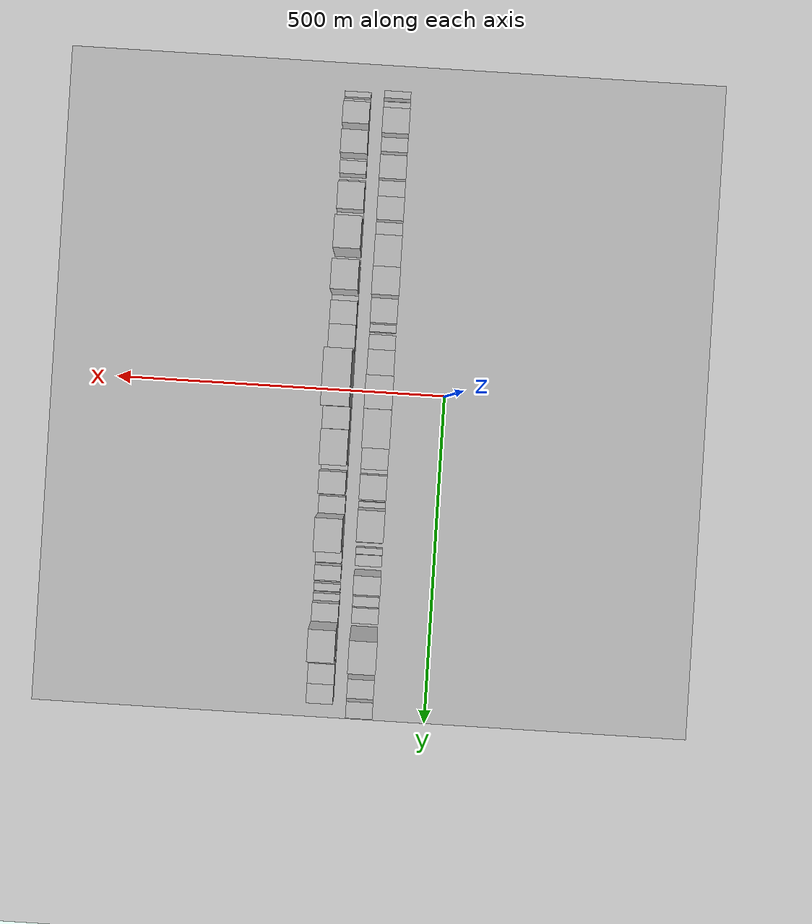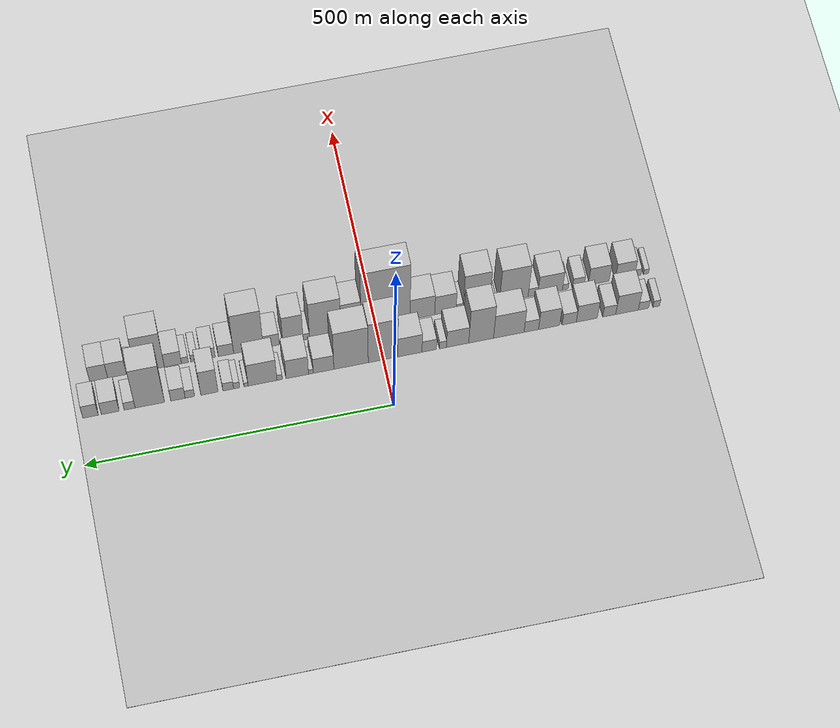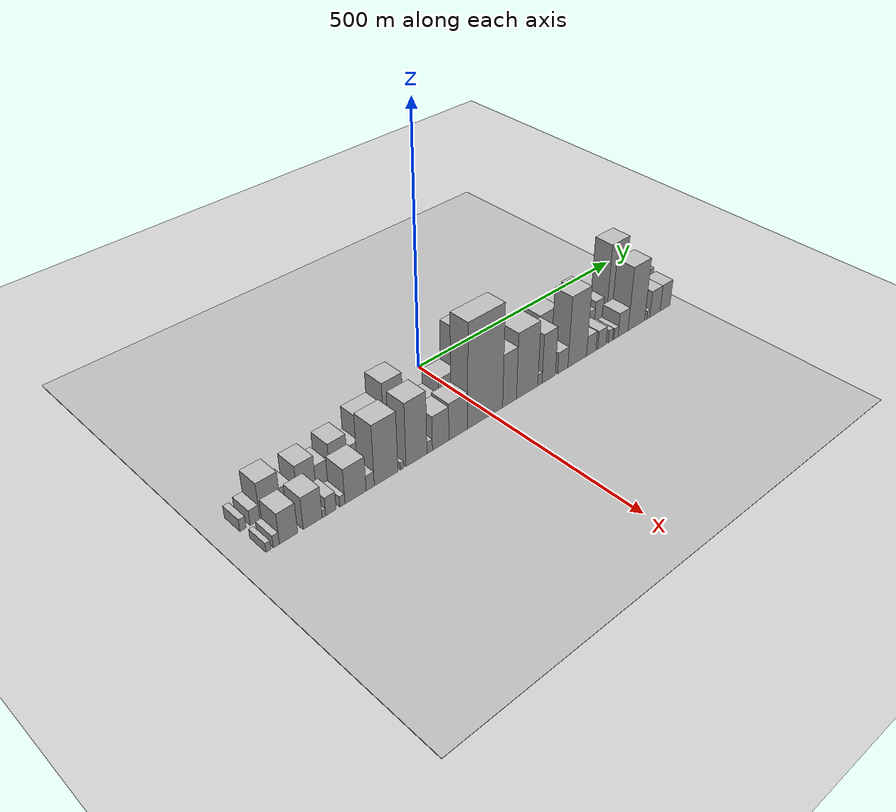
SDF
<?xml version="1.0" encoding="utf-8"?>

<sdf version="1.6">

   <world name="default">

      <gui fullscreen="0">

         <camera name="user_camera">

            <pose>-15 0 4.57585 0 0 0</pose>

            <view_controller>orbit</view_controller>

         </camera>

      </gui>

      <scene>

         <sky>

           <clouds>

             <speed>12</speed>

           </clouds>

         </sky>

         <ambient>0.4 0.4 0.4 1</ambient>

         <background>0.7 0.7 0.7 1</background>

         <shadows>1</shadows>

      </scene>

      <gravity>0 0 -9.8066</gravity>

      <magnetic_field>6e-06 2.3e-05 -4.2e-05</magnetic_field>

      <physics default="0" name="default_physics" type="ode">

         <ode>

            <solver>

               <type>quick</type>

               <iters>10</iters>

               <sor>1.0</sor>

               <use_dynamic_moi_rescaling>0</use_dynamic_moi_rescaling>

            </solver>

            <constraints>

               <cfm>0</cfm>

               <erp>0.2</erp>

               <contact_max_correcting_vel>100</contact_max_correcting_vel>

               <contact_surface_layer>0.001</contact_surface_layer>

            </constraints>

         </ode>

         <max_step_size>0.004</max_step_size>

         <real_time_factor>1</real_time_factor>

         <real_time_update_rate>250</real_time_update_rate>

      </physics>

      <light name="sun" type="directional">

         <cast_shadows>1</cast_shadows>

         <pose>0 0 10 0 0 0</pose>

         <diffuse>0.8 0.8 0.8 1</diffuse>

         <specular>0.2 0.2 0.2 1</specular>

         <attenuation>

            <range>1000</range>

            <constant>0.9</constant>

            <linear>0.01</linear>

            <quadratic>0.001</quadratic>

         </attenuation>

         <direction>-0.5 0.1 -0.9</direction>

      </light>

      <include>

         <name>ground_plane_1</name>

         <uri>model://HANNAS_ground_plane</uri>

         <pose>0 0 0  0 0 0</pose>

      </include>

      <include>

         <name>ground_plane_2</name>

         <uri>model://HANNAS_ground_plane</uri>

         <pose>100 0 0  0 0 0</pose>

      </include>

      <model name="building_1">

         <static>1</static>

         <pose frame="">100.0000 -450.5411 0 0.000000 0.000000 0.000000</pose>

         <link name="link">

            <pose frame="">0 0 12.00 0 0 0</pose>

            <collision name="collision">

               <geometry>

                  <box>

                     <size>40.0000 10.9178 24.0000</size>

                  </box>

               </geometry>

               <max_contacts>10</max_contacts>

               <surface>

                  <contact>

                     <ode/>

                  </contact>

                  <bounce/>

                  <friction>

                     <torsional>

                        <ode/>

                     </torsional>

                     <ode/>

                  </friction>

               </surface>

            </collision>

            <visual name="visual">

               <cast_shadows>0</cast_shadows>

               <geometry>

                  <box>

                     <size>40.0000 10.9178 24.0000</size>

                  </box>

               </geometry>

               <material>

                  <script>

                     <uri>model://HANNAS_wall/materials/scripts</uri>

                     <uri>model://HANNAS_wall/materials/textures</uri>

                     <name>vrc/HANNAS_wall</name>

                  </script>

               </material>

            </visual>

            <self_collide>0</self_collide>

            <enable_wind>0</enable_wind>

            <kinematic>0</kinematic>

         </link>

      </model>

      <model name="building_2">

         <static>1</static>

         <pose frame="">100.0000 -429.3269 0 0.000000 0.000000 0.000000</pose>

         <link name="link">

            <pose frame="">0 0 15.00 0 0 0</pose>

            <collision name="collision">

               <geometry>

                  <box>

                     <size>40.0000 17.5106 30.0000</size>

                  </box>

               </geometry>

               <max_contacts>10</max_contacts>

               <surface>

                  <contact>

                     <ode/>

                  </contact>

                  <bounce/>

                  <friction>

                     <torsional>

                        <ode/>

                     </torsional>

                     <ode/>

                  </friction>

               </surface>

            </collision>

            <visual name="visual">

               <cast_shadows>0</cast_shadows>

               <geometry>

                  <box>

                     <size>40.0000 17.5106 30.0000</size>

                  </box>

               </geometry>

               <material>

                  <script>

                     <uri>model://HANNAS_wall/materials/scripts</uri>

                     <uri>model://HANNAS_wall/materials/textures</uri>

                     <name>vrc/HANNAS_wall</name>

                  </script>

               </material>

            </visual>

            <self_collide>0</self_collide>

            <enable_wind>0</enable_wind>

            <kinematic>0</kinematic>

         </link>

      </model>

      <model name="building_3">

         <static>1</static>

         <pose frame="">100.0000 -401.6771 0 0.000000 0.000000 0.000000</pose>

         <link name="link">

            <pose frame="">0 0 36.00 0 0 0</pose>

            <collision name="collision">

               <geometry>

                  <box>

                     <size>40.0000 37.7890 72.0000</size>

                  </box>

               </geometry>

               <max_contacts>10</max_contacts>

               <surface>

                  <contact>

                     <ode/>

                  </contact>

                  <bounce/>

                  <friction>

                     <torsional>

                        <ode/>

                     </torsional>

                     <ode/>

                  </friction>

               </surface>

            </collision>

            <visual name="visual">

               <cast_shadows>0</cast_shadows>

               <geometry>

                  <box>

                     <size>40.0000 37.7890 72.0000</size>

                  </box>

               </geometry>

               <material>

                  <script>

                     <uri>model://HANNAS_wall/materials/scripts</uri>

                     <uri>model://HANNAS_wall/materials/textures</uri>

                     <name>vrc/HANNAS_wall</name>

                  </script>

               </material>

            </visual>

            <self_collide>0</self_collide>

            <enable_wind>0</enable_wind>

            <kinematic>0</kinematic>

         </link>

      </model>

      <model name="building_4">

         <static>1</static>

         <pose frame="">100.0000 -372.0644 0 0.000000 0.000000 0.000000</pose>

         <link name="link">

            <pose frame="">0 0 19.50 0 0 0</pose>

            <collision name="collision">

               <geometry>

                  <box>

                     <size>40.0000 21.4364 39.0000</size>

                  </box>

               </geometry>

               <max_contacts>10</max_contacts>

               <surface>

                  <contact>

                     <ode/>

                  </contact>

                  <bounce/>

                  <friction>

                     <torsional>

                        <ode/>

                     </torsional>

                     <ode/>

                  </friction>

               </surface>

            </collision>

            <visual name="visual">

               <cast_shadows>0</cast_shadows>

               <geometry>

                  <box>

                     <size>40.0000 21.4364 39.0000</size>

                  </box>

               </geometry>

               <material>

                  <script>

                     <uri>model://HANNAS_wall/materials/scripts</uri>

                     <uri>model://HANNAS_wall/materials/textures</uri>

                     <name>vrc/HANNAS_wall</name>

                  </script>

               </material>

            </visual>

            <self_collide>0</self_collide>

            <enable_wind>0</enable_wind>

            <kinematic>0</kinematic>

         </link>

      </model>

      <model name="building_5">

         <static>1</static>

         <pose frame="">100.0000 -334.7644 0 0.000000 0.000000 0.000000</pose>

         <link name="link">

            <pose frame="">0 0 31.50 0 0 0</pose>

            <collision name="collision">

               <geometry>

                  <box>

                     <size>40.0000 35.1636 63.0000</size>

                  </box>

               </geometry>

               <max_contacts>10</max_contacts>

               <surface>

                  <contact>

                     <ode/>

                  </contact>

                  <bounce/>

                  <friction>

                     <torsional>

                        <ode/>

                     </torsional>

                     <ode/>

                  </friction>

               </surface>

            </collision>

            <visual name="visual">

               <cast_shadows>0</cast_shadows>

               <geometry>

                  <box>

                     <size>40.0000 35.1636 63.0000</size>

                  </box>

               </geometry>

               <material>

                  <script>

                     <uri>model://HANNAS_wall/materials/scripts</uri>

                     <uri>model://HANNAS_wall/materials/textures</uri>

                     <name>vrc/HANNAS_wall</name>

                  </script>

               </material>

            </visual>

            <self_collide>0</self_collide>

            <enable_wind>0</enable_wind>

            <kinematic>0</kinematic>

         </link>

      </model>

      <model name="building_6">

         <static>1</static>

         <pose frame="">100.0000 -305.4327 0 0.000000 0.000000 0.000000</pose>

         <link name="link">

            <pose frame="">0 0 21.00 0 0 0</pose>

            <collision name="collision">

               <geometry>

                  <box>

                     <size>40.0000 23.4999 42.0000</size>

                  </box>

               </geometry>

               <max_contacts>10</max_contacts>

               <surface>

                  <contact>

                     <ode/>

                  </contact>

                  <bounce/>

                  <friction>

                     <torsional>

                        <ode/>

                     </torsional>

                     <ode/>

                  </friction>

               </surface>

            </collision>

            <visual name="visual">

               <cast_shadows>0</cast_shadows>

               <geometry>

                  <box>

                     <size>40.0000 23.4999 42.0000</size>

                  </box>

               </geometry>

               <material>

                  <script>

                     <uri>model://HANNAS_wall/materials/scripts</uri>

                     <uri>model://HANNAS_wall/materials/textures</uri>

                     <name>vrc/HANNAS_wall</name>

                  </script>

               </material>

            </visual>

            <self_collide>0</self_collide>

            <enable_wind>0</enable_wind>

            <kinematic>0</kinematic>

         </link>

      </model>

      <model name="building_7">

         <static>1</static>

         <pose frame="">100.0000 -272.2395 0 0.000000 0.000000 0.000000</pose>

         <link name="link">

            <pose frame="">0 0 34.50 0 0 0</pose>

            <collision name="collision">

               <geometry>

                  <box>

                     <size>40.0000 34.8864 69.0000</size>

                  </box>

               </geometry>

               <max_contacts>10</max_contacts>

               <surface>

                  <contact>

                     <ode/>

                  </contact>

                  <bounce/>

                  <friction>

                     <torsional>

                        <ode/>

                     </torsional>

                     <ode/>

                  </friction>

               </surface>

            </collision>

            <visual name="visual">

               <cast_shadows>0</cast_shadows>

               <geometry>

                  <box>

                     <size>40.0000 34.8864 69.0000</size>

                  </box>

               </geometry>

               <material>

                  <script>

                     <uri>model://HANNAS_wall/materials/scripts</uri>

                     <uri>model://HANNAS_wall/materials/textures</uri>

                     <name>vrc/HANNAS_wall</name>

                  </script>

               </material>

            </visual>

            <self_collide>0</self_collide>

            <enable_wind>0</enable_wind>

            <kinematic>0</kinematic>

         </link>

      </model>

      <model name="building_8">

         <static>1</static>

         <pose frame="">100.0000 -242.7471 0 0.000000 0.000000 0.000000</pose>

         <link name="link">

            <pose frame="">0 0 21.00 0 0 0</pose>

            <collision name="collision">

               <geometry>

                  <box>

                     <size>40.0000 24.0984 42.0000</size>

                  </box>

               </geometry>

               <max_contacts>10</max_contacts>

               <surface>

                  <contact>

                     <ode/>

                  </contact>

                  <bounce/>

                  <friction>

                     <torsional>

                        <ode/>

                     </torsional>

                     <ode/>

                  </friction>

               </surface>

            </collision>

            <visual name="visual">

               <cast_shadows>0</cast_shadows>

               <geometry>

                  <box>

                     <size>40.0000 24.0984 42.0000</size>

                  </box>

               </geometry>

               <material>

                  <script>

                     <uri>model://HANNAS_wall/materials/scripts</uri>

                     <uri>model://HANNAS_wall/materials/textures</uri>

                     <name>vrc/HANNAS_wall</name>

                  </script>

               </material>

            </visual>

            <self_collide>0</self_collide>

            <enable_wind>0</enable_wind>

            <kinematic>0</kinematic>

         </link>

      </model>

      <model name="building_9">

         <static>1</static>

         <pose frame="">100.0000 -205.4425 0 0.000000 0.000000 0.000000</pose>

         <link name="link">

            <pose frame="">0 0 43.50 0 0 0</pose>

            <collision name="collision">

               <geometry>

                  <box>

                     <size>40.0000 50.5108 87.0000</size>

                  </box>

               </geometry>

               <max_contacts>10</max_contacts>

               <surface>

                  <contact>

                     <ode/>

                  </contact>

                  <bounce/>

                  <friction>

                     <torsional>

                        <ode/>

                     </torsional>

                     <ode/>

                  </friction>

               </surface>

            </collision>

            <visual name="visual">

               <cast_shadows>0</cast_shadows>

               <geometry>

                  <box>

                     <size>40.0000 50.5108 87.0000</size>

                  </box>

               </geometry>

               <material>

                  <script>

                     <uri>model://HANNAS_wall/materials/scripts</uri>

                     <uri>model://HANNAS_wall/materials/textures</uri>

                     <name>vrc/HANNAS_wall</name>

                  </script>

               </material>

            </visual>

            <self_collide>0</self_collide>

            <enable_wind>0</enable_wind>

            <kinematic>0</kinematic>

         </link>

      </model>

      <model name="building_10">

         <static>1</static>

         <pose frame="">100.0000 -159.7192 0 0.000000 0.000000 0.000000</pose>

         <link name="link">

            <pose frame="">0 0 63.00 0 0 0</pose>

            <collision name="collision">

               <geometry>

                  <box>

                     <size>40.0000 40.9357 126.0000</size>

                  </box>

               </geometry>

               <max_contacts>10</max_contacts>

               <surface>

                  <contact>

                     <ode/>

                  </contact>

                  <bounce/>

                  <friction>

                     <torsional>

                        <ode/>

                     </torsional>

                     <ode/>

                  </friction>

               </surface>

            </collision>

            <visual name="visual">

               <cast_shadows>0</cast_shadows>

               <geometry>

                  <box>

                     <size>40.0000 40.9357 126.0000</size>

                  </box>

               </geometry>

               <material>

                  <script>

                     <uri>model://HANNAS_wall/materials/scripts</uri>

                     <uri>model://HANNAS_wall/materials/textures</uri>

                     <name>vrc/HANNAS_wall</name>

                  </script>

               </material>

            </visual>

            <self_collide>0</self_collide>

            <enable_wind>0</enable_wind>

            <kinematic>0</kinematic>

         </link>

      </model>

      <model name="building_11">

         <static>1</static>

         <pose frame="">100.0000 -120.8370 0 0.000000 0.000000 0.000000</pose>

         <link name="link">

            <pose frame="">0 0 31.50 0 0 0</pose>

            <collision name="collision">

               <geometry>

                  <box>

                     <size>40.0000 36.8287 63.0000</size>

                  </box>

               </geometry>

               <max_contacts>10</max_contacts>

               <surface>

                  <contact>

                     <ode/>

                  </contact>

                  <bounce/>

                  <friction>

                     <torsional>

                        <ode/>

                     </torsional>

                     <ode/>

                  </friction>

               </surface>

            </collision>

            <visual name="visual">

               <cast_shadows>0</cast_shadows>

               <geometry>

                  <box>

                     <size>40.0000 36.8287 63.0000</size>

                  </box>

               </geometry>

               <material>

                  <script>

                     <uri>model://HANNAS_wall/materials/scripts</uri>

                     <uri>model://HANNAS_wall/materials/textures</uri>

                     <name>vrc/HANNAS_wall</name>

                  </script>

               </material>

            </visual>

            <self_collide>0</self_collide>

            <enable_wind>0</enable_wind>

            <kinematic>0</kinematic>

         </link>

      </model>

      <model name="building_12">

         <static>1</static>

         <pose frame="">100.0000 -96.7278 0 0.000000 0.000000 0.000000</pose>

         <link name="link">

            <pose frame="">0 0 13.50 0 0 0</pose>

            <collision name="collision">

               <geometry>

                  <box>

                     <size>40.0000 11.3897 27.0000</size>

                  </box>

               </geometry>

               <max_contacts>10</max_contacts>

               <surface>

                  <contact>

                     <ode/>

                  </contact>

                  <bounce/>

                  <friction>

                     <torsional>

                        <ode/>

                     </torsional>

                     <ode/>

                  </friction>

               </surface>

            </collision>

            <visual name="visual">

               <cast_shadows>0</cast_shadows>

               <geometry>

                  <box>

                     <size>40.0000 11.3897 27.0000</size>

                  </box>

               </geometry>

               <material>

                  <script>

                     <uri>model://HANNAS_wall/materials/scripts</uri>

                     <uri>model://HANNAS_wall/materials/textures</uri>

                     <name>vrc/HANNAS_wall</name>

                  </script>

               </material>

            </visual>

            <self_collide>0</self_collide>

            <enable_wind>0</enable_wind>

            <kinematic>0</kinematic>

         </link>

      </model>

      <model name="building_13">

         <static>1</static>

         <pose frame="">100.0000 -74.1513 0 0.000000 0.000000 0.000000</pose>

         <link name="link">

            <pose frame="">0 0 21.00 0 0 0</pose>

            <collision name="collision">

               <geometry>

                  <box>

                     <size>40.0000 23.7634 42.0000</size>

                  </box>

               </geometry>

               <max_contacts>10</max_contacts>

               <surface>

                  <contact>

                     <ode/>

                  </contact>

                  <bounce/>

                  <friction>

                     <torsional>

                        <ode/>

                     </torsional>

                     <ode/>

                  </friction>

               </surface>

            </collision>

            <visual name="visual">

               <cast_shadows>0</cast_shadows>

               <geometry>

                  <box>

                     <size>40.0000 23.7634 42.0000</size>

                  </box>

               </geometry>

               <material>

                  <script>

                     <uri>model://HANNAS_wall/materials/scripts</uri>

                     <uri>model://HANNAS_wall/materials/textures</uri>

                     <name>vrc/HANNAS_wall</name>

                  </script>

               </material>

            </visual>

            <self_collide>0</self_collide>

            <enable_wind>0</enable_wind>

            <kinematic>0</kinematic>

         </link>

      </model>

      <model name="building_14">

         <static>1</static>

         <pose frame="">100.0000 -42.3100 0 0.000000 0.000000 0.000000</pose>

         <link name="link">

            <pose frame="">0 0 36.00 0 0 0</pose>

            <collision name="collision">

               <geometry>

                  <box>

                     <size>40.0000 39.9191 72.0000</size>

                  </box>

               </geometry>

               <max_contacts>10</max_contacts>

               <surface>

                  <contact>

                     <ode/>

                  </contact>

                  <bounce/>

                  <friction>

                     <torsional>

                        <ode/>

                     </torsional>

                     <ode/>

                  </friction>

               </surface>

            </collision>

            <visual name="visual">

               <cast_shadows>0</cast_shadows>

               <geometry>

                  <box>

                     <size>40.0000 39.9191 72.0000</size>

                  </box>

               </geometry>

               <material>

                  <script>

                     <uri>model://HANNAS_wall/materials/scripts</uri>

                     <uri>model://HANNAS_wall/materials/textures</uri>

                     <name>vrc/HANNAS_wall</name>

                  </script>

               </material>

            </visual>

            <self_collide>0</self_collide>

            <enable_wind>0</enable_wind>

            <kinematic>0</kinematic>

         </link>

      </model>

      <model name="building_15">

         <static>1</static>

         <pose frame="">100.0000 1.8041 0 0.000000 0.000000 0.000000</pose>

         <link name="link">

            <pose frame="">0 0 75.00 0 0 0</pose>

            <collision name="collision">

               <geometry>

                  <box>

                     <size>40.0000 48.3091 150.0000</size>

                  </box>

               </geometry>

               <max_contacts>10</max_contacts>

               <surface>

                  <contact>

                     <ode/>

                  </contact>

                  <bounce/>

                  <friction>

                     <torsional>

                        <ode/>

                     </torsional>

                     <ode/>

                  </friction>

               </surface>

            </collision>

            <visual name="visual">

               <cast_shadows>0</cast_shadows>

               <geometry>

                  <box>

                     <size>40.0000 48.3091 150.0000</size>

                  </box>

               </geometry>

               <material>

                  <script>

                     <uri>model://HANNAS_wall/materials/scripts</uri>

                     <uri>model://HANNAS_wall/materials/textures</uri>

                     <name>vrc/HANNAS_wall</name>

                  </script>

               </material>

            </visual>

            <self_collide>0</self_collide>

            <enable_wind>0</enable_wind>

            <kinematic>0</kinematic>

         </link>

      </model>

      <model name="building_16">

         <static>1</static>

         <pose frame="">100.0000 54.0639 0 0.000000 0.000000 0.000000</pose>

         <link name="link">

            <pose frame="">0 0 70.50 0 0 0</pose>

            <collision name="collision">

               <geometry>

                  <box>

                     <size>40.0000 56.2105 141.0000</size>

                  </box>

               </geometry>

               <max_contacts>10</max_contacts>

               <surface>

                  <contact>

                     <ode/>

                  </contact>

                  <bounce/>

                  <friction>

                     <torsional>

                        <ode/>

                     </torsional>

                     <ode/>

                  </friction>

               </surface>

            </collision>

            <visual name="visual">

               <cast_shadows>0</cast_shadows>

               <geometry>

                  <box>

                     <size>40.0000 56.2105 141.0000</size>

                  </box>

               </geometry>

               <material>

                  <script>

                     <uri>model://HANNAS_wall/materials/scripts</uri>

                     <uri>model://HANNAS_wall/materials/textures</uri>

                     <name>vrc/HANNAS_wall</name>

                  </script>

               </material>

            </visual>

            <self_collide>0</self_collide>

            <enable_wind>0</enable_wind>

            <kinematic>0</kinematic>

         </link>

      </model>

      <model name="building_17">

         <static>1</static>

         <pose frame="">100.0000 99.0223 0 0.000000 0.000000 0.000000</pose>

         <link name="link">

            <pose frame="">0 0 28.50 0 0 0</pose>

            <collision name="collision">

               <geometry>

                  <box>

                     <size>40.0000 33.7064 57.0000</size>

                  </box>

               </geometry>

               <max_contacts>10</max_contacts>

               <surface>

                  <contact>

                     <ode/>

                  </contact>

                  <bounce/>

                  <friction>

                     <torsional>

                        <ode/>

                     </torsional>

                     <ode/>

                  </friction>

               </surface>

            </collision>

            <visual name="visual">

               <cast_shadows>0</cast_shadows>

               <geometry>

                  <box>

                     <size>40.0000 33.7064 57.0000</size>

                  </box>

               </geometry>

               <material>

                  <script>

                     <uri>model://HANNAS_wall/materials/scripts</uri>

                     <uri>model://HANNAS_wall/materials/textures</uri>

                     <name>vrc/HANNAS_wall</name>

                  </script>

               </material>

            </visual>

            <self_collide>0</self_collide>

            <enable_wind>0</enable_wind>

            <kinematic>0</kinematic>

         </link>

      </model>

      <model name="building_18">

         <static>1</static>

         <pose frame="">100.0000 119.7152 0 0.000000 0.000000 0.000000</pose>

         <link name="link">

            <pose frame="">0 0 9.00 0 0 0</pose>

            <collision name="collision">

               <geometry>

                  <box>

                     <size>40.0000 7.6794 18.0000</size>

                  </box>

               </geometry>

               <max_contacts>10</max_contacts>

               <surface>

                  <contact>

                     <ode/>

                  </contact>

                  <bounce/>

                  <friction>

                     <torsional>

                        <ode/>

                     </torsional>

                     <ode/>

                  </friction>

               </surface>

            </collision>

            <visual name="visual">

               <cast_shadows>0</cast_shadows>

               <geometry>

                  <box>

                     <size>40.0000 7.6794 18.0000</size>

                  </box>

               </geometry>

               <material>

                  <script>

                     <uri>model://HANNAS_wall/materials/scripts</uri>

                     <uri>model://HANNAS_wall/materials/textures</uri>

                     <name>vrc/HANNAS_wall</name>

                  </script>

               </material>

            </visual>

            <self_collide>0</self_collide>

            <enable_wind>0</enable_wind>

            <kinematic>0</kinematic>

         </link>

      </model>

      <model name="building_19">

         <static>1</static>

         <pose frame="">100.0000 141.9152 0 0.000000 0.000000 0.000000</pose>

         <link name="link">

            <pose frame="">0 0 36.00 0 0 0</pose>

            <collision name="collision">

               <geometry>

                  <box>

                     <size>40.0000 36.7206 72.0000</size>

                  </box>

               </geometry>

               <max_contacts>10</max_contacts>

               <surface>

                  <contact>

                     <ode/>

                  </contact>

                  <bounce/>

                  <friction>

                     <torsional>

                        <ode/>

                     </torsional>

                     <ode/>

                  </friction>

               </surface>

            </collision>

            <visual name="visual">

               <cast_shadows>0</cast_shadows>

               <geometry>

                  <box>

                     <size>40.0000 36.7206 72.0000</size>

                  </box>

               </geometry>

               <material>

                  <script>

                     <uri>model://HANNAS_wall/materials/scripts</uri>

                     <uri>model://HANNAS_wall/materials/textures</uri>

                     <name>vrc/HANNAS_wall</name>

                  </script>

               </material>

            </visual>

            <self_collide>0</self_collide>

            <enable_wind>0</enable_wind>

            <kinematic>0</kinematic>

         </link>

      </model>

      <model name="building_20">

         <static>1</static>

         <pose frame="">100.0000 170.6865 0 0.000000 0.000000 0.000000</pose>

         <link name="link">

            <pose frame="">0 0 10.50 0 0 0</pose>

            <collision name="collision">

               <geometry>

                  <box>

                     <size>40.0000 8.8220 21.0000</size>

                  </box>

               </geometry>

               <max_contacts>10</max_contacts>

               <surface>

                  <contact>

                     <ode/>

                  </contact>

                  <bounce/>

                  <friction>

                     <torsional>

                        <ode/>

                     </torsional>

                     <ode/>

                  </friction>

               </surface>

            </collision>

            <visual name="visual">

               <cast_shadows>0</cast_shadows>

               <geometry>

                  <box>

                     <size>40.0000 8.8220 21.0000</size>

                  </box>

               </geometry>

               <material>

                  <script>

                     <uri>model://HANNAS_wall/materials/scripts</uri>

                     <uri>model://HANNAS_wall/materials/textures</uri>

                     <name>vrc/HANNAS_wall</name>

                  </script>

               </material>

            </visual>

            <self_collide>0</self_collide>

            <enable_wind>0</enable_wind>

            <kinematic>0</kinematic>

         </link>

      </model>

      <model name="building_21">

         <static>1</static>

         <pose frame="">100.0000 198.5647 0 0.000000 0.000000 0.000000</pose>

         <link name="link">

            <pose frame="">0 0 42.00 0 0 0</pose>

            <collision name="collision">

               <geometry>

                  <box>

                     <size>40.0000 46.9344 84.0000</size>

                  </box>

               </geometry>

               <max_contacts>10</max_contacts>

               <surface>

                  <contact>

                     <ode/>

                  </contact>

                  <bounce/>

                  <friction>

                     <torsional>

                        <ode/>

                     </torsional>

                     <ode/>

                  </friction>

               </surface>

            </collision>

            <visual name="visual">

               <cast_shadows>0</cast_shadows>

               <geometry>

                  <box>

                     <size>40.0000 46.9344 84.0000</size>

                  </box>

               </geometry>

               <material>

                  <script>

                     <uri>model://HANNAS_wall/materials/scripts</uri>

                     <uri>model://HANNAS_wall/materials/textures</uri>

                     <name>vrc/HANNAS_wall</name>

                  </script>

               </material>

            </visual>

            <self_collide>0</self_collide>

            <enable_wind>0</enable_wind>

            <kinematic>0</kinematic>

         </link>

      </model>

      <model name="building_22">

         <static>1</static>

         <pose frame="">100.0000 225.3396 0 0.000000 0.000000 0.000000</pose>

         <link name="link">

            <pose frame="">0 0 7.50 0 0 0</pose>

            <collision name="collision">

               <geometry>

                  <box>

                     <size>40.0000 6.6154 15.0000</size>

                  </box>

               </geometry>

               <max_contacts>10</max_contacts>

               <surface>

                  <contact>

                     <ode/>

                  </contact>

                  <bounce/>

                  <friction>

                     <torsional>

                        <ode/>

                     </torsional>

                     <ode/>

                  </friction>

               </surface>

            </collision>

            <visual name="visual">

               <cast_shadows>0</cast_shadows>

               <geometry>

                  <box>

                     <size>40.0000 6.6154 15.0000</size>

                  </box>

               </geometry>

               <material>

                  <script>

                     <uri>model://HANNAS_wall/materials/scripts</uri>

                     <uri>model://HANNAS_wall/materials/textures</uri>

                     <name>vrc/HANNAS_wall</name>

                  </script>

               </material>

            </visual>

            <self_collide>0</self_collide>

            <enable_wind>0</enable_wind>

            <kinematic>0</kinematic>

         </link>

      </model>

      <model name="building_23">

         <static>1</static>

         <pose frame="">100.0000 240.6629 0 0.000000 0.000000 0.000000</pose>

         <link name="link">

            <pose frame="">0 0 12.00 0 0 0</pose>

            <collision name="collision">

               <geometry>

                  <box>

                     <size>40.0000 10.0314 24.0000</size>

                  </box>

               </geometry>

               <max_contacts>10</max_contacts>

               <surface>

                  <contact>

                     <ode/>

                  </contact>

                  <bounce/>

                  <friction>

                     <torsional>

                        <ode/>

                     </torsional>

                     <ode/>

                  </friction>

               </surface>

            </collision>

            <visual name="visual">

               <cast_shadows>0</cast_shadows>

               <geometry>

                  <box>

                     <size>40.0000 10.0314 24.0000</size>

                  </box>

               </geometry>

               <material>

                  <script>

                     <uri>model://HANNAS_wall/materials/scripts</uri>

                     <uri>model://HANNAS_wall/materials/textures</uri>

                     <name>vrc/HANNAS_wall</name>

                  </script>

               </material>

            </visual>

            <self_collide>0</self_collide>

            <enable_wind>0</enable_wind>

            <kinematic>0</kinematic>

         </link>

      </model>

      <model name="building_24">

         <static>1</static>

         <pose frame="">100.0000 254.2844 0 0.000000 0.000000 0.000000</pose>

         <link name="link">

            <pose frame="">0 0 15.00 0 0 0</pose>

            <collision name="collision">

               <geometry>

                  <box>

                     <size>40.0000 17.2115 30.0000</size>

                  </box>

               </geometry>

               <max_contacts>10</max_contacts>

               <surface>

                  <contact>

                     <ode/>

                  </contact>

                  <bounce/>

                  <friction>

                     <torsional>

                        <ode/>

                     </torsional>

                     <ode/>

                  </friction>

               </surface>

            </collision>

            <visual name="visual">

               <cast_shadows>0</cast_shadows>

               <geometry>

                  <box>

                     <size>40.0000 17.2115 30.0000</size>

                  </box>

               </geometry>

               <material>

                  <script>

                     <uri>model://HANNAS_wall/materials/scripts</uri>

                     <uri>model://HANNAS_wall/materials/textures</uri>

                     <name>vrc/HANNAS_wall</name>

                  </script>

               </material>

            </visual>

            <self_collide>0</self_collide>

            <enable_wind>0</enable_wind>

            <kinematic>0</kinematic>

         </link>

      </model>

      <model name="building_25">

         <static>1</static>

         <pose frame="">100.0000 284.8559 0 0.000000 0.000000 0.000000</pose>

         <link name="link">

            <pose frame="">0 0 46.50 0 0 0</pose>

            <collision name="collision">

               <geometry>

                  <box>

                     <size>40.0000 27.9316 93.0000</size>

                  </box>

               </geometry>

               <max_contacts>10</max_contacts>

               <surface>

                  <contact>

                     <ode/>

                  </contact>

                  <bounce/>

                  <friction>

                     <torsional>

                        <ode/>

                     </torsional>

                     <ode/>

                  </friction>

               </surface>

            </collision>

            <visual name="visual">

               <cast_shadows>0</cast_shadows>

               <geometry>

                  <box>

                     <size>40.0000 27.9316 93.0000</size>

                  </box>

               </geometry>

               <material>

                  <script>

                     <uri>model://HANNAS_wall/materials/scripts</uri>

                     <uri>model://HANNAS_wall/materials/textures</uri>

                     <name>vrc/HANNAS_wall</name>

                  </script>

               </material>

            </visual>

            <self_collide>0</self_collide>

            <enable_wind>0</enable_wind>

            <kinematic>0</kinematic>

         </link>

      </model>

      <model name="building_26">

         <static>1</static>

         <pose frame="">100.0000 316.4387 0 0.000000 0.000000 0.000000</pose>

         <link name="link">

            <pose frame="">0 0 15.00 0 0 0</pose>

            <collision name="collision">

               <geometry>

                  <box>

                     <size>40.0000 15.2339 30.0000</size>

                  </box>

               </geometry>

               <max_contacts>10</max_contacts>

               <surface>

                  <contact>

                     <ode/>

                  </contact>

                  <bounce/>

                  <friction>

                     <torsional>

                        <ode/>

                     </torsional>

                     <ode/>

                  </friction>

               </surface>

            </collision>

            <visual name="visual">

               <cast_shadows>0</cast_shadows>

               <geometry>

                  <box>

                     <size>40.0000 15.2339 30.0000</size>

                  </box>

               </geometry>

               <material>

                  <script>

                     <uri>model://HANNAS_wall/materials/scripts</uri>

                     <uri>model://HANNAS_wall/materials/textures</uri>

                     <name>vrc/HANNAS_wall</name>

                  </script>

               </material>

            </visual>

            <self_collide>0</self_collide>

            <enable_wind>0</enable_wind>

            <kinematic>0</kinematic>

         </link>

      </model>

      <model name="building_27">

         <static>1</static>

         <pose frame="">100.0000 335.7708 0 0.000000 0.000000 0.000000</pose>

         <link name="link">

            <pose frame="">0 0 22.50 0 0 0</pose>

            <collision name="collision">

               <geometry>

                  <box>

                     <size>40.0000 23.4305 45.0000</size>

                  </box>

               </geometry>

               <max_contacts>10</max_contacts>

               <surface>

                  <contact>

                     <ode/>

                  </contact>

                  <bounce/>

                  <friction>

                     <torsional>

                        <ode/>

                     </torsional>

                     <ode/>

                  </friction>

               </surface>

            </collision>

            <visual name="visual">

               <cast_shadows>0</cast_shadows>

               <geometry>

                  <box>

                     <size>40.0000 23.4305 45.0000</size>

                  </box>

               </geometry>

               <material>

                  <script>

                     <uri>model://HANNAS_wall/materials/scripts</uri>

                     <uri>model://HANNAS_wall/materials/textures</uri>

                     <name>vrc/HANNAS_wall</name>

                  </script>

               </material>

            </visual>

            <self_collide>0</self_collide>

            <enable_wind>0</enable_wind>

            <kinematic>0</kinematic>

         </link>

      </model>

      <model name="building_28">

         <static>1</static>

         <pose frame="">100.0000 381.2269 0 0.000000 0.000000 0.000000</pose>

         <link name="link">

            <pose frame="">0 0 75.00 0 0 0</pose>

            <collision name="collision">

               <geometry>

                  <box>

                     <size>40.0000 47.4817 150.0000</size>

                  </box>

               </geometry>

               <max_contacts>10</max_contacts>

               <surface>

                  <contact>

                     <ode/>

                  </contact>

                  <bounce/>

                  <friction>

                     <torsional>

                        <ode/>

                     </torsional>

                     <ode/>

                  </friction>

               </surface>

            </collision>

            <visual name="visual">

               <cast_shadows>0</cast_shadows>

               <geometry>

                  <box>

                     <size>40.0000 47.4817 150.0000</size>

                  </box>

               </geometry>

               <material>

                  <script>

                     <uri>model://HANNAS_wall/materials/scripts</uri>

                     <uri>model://HANNAS_wall/materials/textures</uri>

                     <name>vrc/HANNAS_wall</name>

                  </script>

               </material>

            </visual>

            <self_collide>0</self_collide>

            <enable_wind>0</enable_wind>

            <kinematic>0</kinematic>

         </link>

      </model>

      <model name="building_29">

         <static>1</static>

         <pose frame="">100.0000 413.8566 0 0.000000 0.000000 0.000000</pose>

         <link name="link">

            <pose frame="">0 0 15.00 0 0 0</pose>

            <collision name="collision">

               <geometry>

                  <box>

                     <size>40.0000 17.7777 30.0000</size>

                  </box>

               </geometry>

               <max_contacts>10</max_contacts>

               <surface>

                  <contact>

                     <ode/>

                  </contact>

                  <bounce/>

                  <friction>

                     <torsional>

                        <ode/>

                     </torsional>

                     <ode/>

                  </friction>

               </surface>

            </collision>

            <visual name="visual">

               <cast_shadows>0</cast_shadows>

               <geometry>

                  <box>

                     <size>40.0000 17.7777 30.0000</size>

                  </box>

               </geometry>

               <material>

                  <script>

                     <uri>model://HANNAS_wall/materials/scripts</uri>

                     <uri>model://HANNAS_wall/materials/textures</uri>

                     <name>vrc/HANNAS_wall</name>

                  </script>

               </material>

            </visual>

            <self_collide>0</self_collide>

            <enable_wind>0</enable_wind>

            <kinematic>0</kinematic>

         </link>

      </model>

      <model name="building_30">

         <static>1</static>

         <pose frame="">100.0000 445.0849 0 0.000000 0.000000 0.000000</pose>

         <link name="link">

            <pose frame="">0 0 24.00 0 0 0</pose>

            <collision name="collision">

               <geometry>

                  <box>

                     <size>40.0000 28.6789 48.0000</size>

                  </box>

               </geometry>

               <max_contacts>10</max_contacts>

               <surface>

                  <contact>

                     <ode/>

                  </contact>

                  <bounce/>

                  <friction>

                     <torsional>

                        <ode/>

                     </torsional>

                     <ode/>

                  </friction>

               </surface>

            </collision>

            <visual name="visual">

               <cast_shadows>0</cast_shadows>

               <geometry>

                  <box>

                     <size>40.0000 28.6789 48.0000</size>

                  </box>

               </geometry>

               <material>

                  <script>

                     <uri>model://HANNAS_wall/materials/scripts</uri>

                     <uri>model://HANNAS_wall/materials/textures</uri>

                     <name>vrc/HANNAS_wall</name>

                  </script>

               </material>

            </visual>

            <self_collide>0</self_collide>

            <enable_wind>0</enable_wind>

            <kinematic>0</kinematic>

         </link>

      </model>

      <model name="building_31">

         <static>1</static>

         <pose frame="">100.0000 476.7768 0 0.000000 0.000000 0.000000</pose>

         <link name="link">

            <pose frame="">0 0 24.00 0 0 0</pose>

            <collision name="collision">

               <geometry>

                  <box>

                     <size>40.0000 24.7049 48.0000</size>

                  </box>

               </geometry>

               <max_contacts>10</max_contacts>

               <surface>

                  <contact>

                     <ode/>

                  </contact>

                  <bounce/>

                  <friction>

                     <torsional>

                        <ode/>

                     </torsional>

                     <ode/>

                  </friction>

               </surface>

            </collision>

            <visual name="visual">

               <cast_shadows>0</cast_shadows>

               <geometry>

                  <box>

                     <size>40.0000 24.7049 48.0000</size>

                  </box>

               </geometry>

               <material>

                  <script>

                     <uri>model://HANNAS_wall/materials/scripts</uri>

                     <uri>model://HANNAS_wall/materials/textures</uri>

                     <name>vrc/HANNAS_wall</name>

                  </script>

               </material>

            </visual>

            <self_collide>0</self_collide>

            <enable_wind>0</enable_wind>

            <kinematic>0</kinematic>

         </link>

      </model>

      <model name="building_32">

         <static>1</static>

         <pose frame="">160.0000 -448.6792 0 0.000000 0.000000 0.000000</pose>

         <link name="link">

            <pose frame="">0 0 9.00 0 0 0</pose>

            <collision name="collision">

               <geometry>

                  <box>

                     <size>40.0000 8.6415 18.0000</size>

                  </box>

               </geometry>

               <max_contacts>10</max_contacts>

               <surface>

                  <contact>

                     <ode/>

                  </contact>

                  <bounce/>

                  <friction>

                     <torsional>

                        <ode/>

                     </torsional>

                     <ode/>

                  </friction>

               </surface>

            </collision>

            <visual name="visual">

               <cast_shadows>0</cast_shadows>

               <geometry>

                  <box>

                     <size>40.0000 8.6415 18.0000</size>

                  </box>

               </geometry>

               <material>

                  <script>

                     <uri>model://HANNAS_wall/materials/scripts</uri>

                     <uri>model://HANNAS_wall/materials/textures</uri>

                     <name>vrc/HANNAS_wall</name>

                  </script>

               </material>

            </visual>

            <self_collide>0</self_collide>

            <enable_wind>0</enable_wind>

            <kinematic>0</kinematic>

         </link>

      </model>

      <model name="building_33">

         <static>1</static>

         <pose frame="">160.0000 -434.9047 0 0.000000 0.000000 0.000000</pose>

         <link name="link">

            <pose frame="">0 0 12.00 0 0 0</pose>

            <collision name="collision">

               <geometry>

                  <box>

                     <size>40.0000 10.9076 24.0000</size>

                  </box>

               </geometry>

               <max_contacts>10</max_contacts>

               <surface>

                  <contact>

                     <ode/>

                  </contact>

                  <bounce/>

                  <friction>

                     <torsional>

                        <ode/>

                     </torsional>

                     <ode/>

                  </friction>

               </surface>

            </collision>

            <visual name="visual">

               <cast_shadows>0</cast_shadows>

               <geometry>

                  <box>

                     <size>40.0000 10.9076 24.0000</size>

                  </box>

               </geometry>

               <material>

                  <script>

                     <uri>model://HANNAS_wall/materials/scripts</uri>

                     <uri>model://HANNAS_wall/materials/textures</uri>

                     <name>vrc/HANNAS_wall</name>

                  </script>

               </material>

            </visual>

            <self_collide>0</self_collide>

            <enable_wind>0</enable_wind>

            <kinematic>0</kinematic>

         </link>

      </model>

      <model name="building_34">

         <static>1</static>

         <pose frame="">160.0000 -413.0833 0 0.000000 0.000000 0.000000</pose>

         <link name="link">

            <pose frame="">0 0 30.00 0 0 0</pose>

            <collision name="collision">

               <geometry>

                  <box>

                     <size>40.0000 32.7351 60.0000</size>

                  </box>

               </geometry>

               <max_contacts>10</max_contacts>

               <surface>

                  <contact>

                     <ode/>

                  </contact>

                  <bounce/>

                  <friction>

                     <torsional>

                        <ode/>

                     </torsional>

                     <ode/>

                  </friction>

               </surface>

            </collision>

            <visual name="visual">

               <cast_shadows>0</cast_shadows>

               <geometry>

                  <box>

                     <size>40.0000 32.7351 60.0000</size>

                  </box>

               </geometry>

               <material>

                  <script>

                     <uri>model://HANNAS_wall/materials/scripts</uri>

                     <uri>model://HANNAS_wall/materials/textures</uri>

                     <name>vrc/HANNAS_wall</name>

                  </script>

               </material>

            </visual>

            <self_collide>0</self_collide>

            <enable_wind>0</enable_wind>

            <kinematic>0</kinematic>

         </link>

      </model>

      <model name="building_35">

         <static>1</static>

         <pose frame="">160.0000 -369.2167 0 0.000000 0.000000 0.000000</pose>

         <link name="link">

            <pose frame="">0 0 31.50 0 0 0</pose>

            <collision name="collision">

               <geometry>

                  <box>

                     <size>40.0000 34.9982 63.0000</size>

                  </box>

               </geometry>

               <max_contacts>10</max_contacts>

               <surface>

                  <contact>

                     <ode/>

                  </contact>

                  <bounce/>

                  <friction>

                     <torsional>

                        <ode/>

                     </torsional>

                     <ode/>

                  </friction>

               </surface>

            </collision>

            <visual name="visual">

               <cast_shadows>0</cast_shadows>

               <geometry>

                  <box>

                     <size>40.0000 34.9982 63.0000</size>

                  </box>

               </geometry>

               <material>

                  <script>

                     <uri>model://HANNAS_wall/materials/scripts</uri>

                     <uri>model://HANNAS_wall/materials/textures</uri>

                     <name>vrc/HANNAS_wall</name>

                  </script>

               </material>

            </visual>

            <self_collide>0</self_collide>

            <enable_wind>0</enable_wind>

            <kinematic>0</kinematic>

         </link>

      </model>

      <model name="building_36">

         <static>1</static>

         <pose frame="">160.0000 -348.4336 0 0.000000 0.000000 0.000000</pose>

         <link name="link">

            <pose frame="">0 0 7.50 0 0 0</pose>

            <collision name="collision">

               <geometry>

                  <box>

                     <size>40.0000 6.5679 15.0000</size>

                  </box>

               </geometry>

               <max_contacts>10</max_contacts>

               <surface>

                  <contact>

                     <ode/>

                  </contact>

                  <bounce/>

                  <friction>

                     <torsional>

                        <ode/>

                     </torsional>

                     <ode/>

                  </friction>

               </surface>

            </collision>

            <visual name="visual">

               <cast_shadows>0</cast_shadows>

               <geometry>

                  <box>

                     <size>40.0000 6.5679 15.0000</size>

                  </box>

               </geometry>

               <material>

                  <script>

                     <uri>model://HANNAS_wall/materials/scripts</uri>

                     <uri>model://HANNAS_wall/materials/textures</uri>

                     <name>vrc/HANNAS_wall</name>

                  </script>

               </material>

            </visual>

            <self_collide>0</self_collide>

            <enable_wind>0</enable_wind>

            <kinematic>0</kinematic>

         </link>

      </model>

      <model name="building_37">

         <static>1</static>

         <pose frame="">160.0000 -335.2588 0 0.000000 0.000000 0.000000</pose>

         <link name="link">

            <pose frame="">0 0 18.00 0 0 0</pose>

            <collision name="collision">

               <geometry>

                  <box>

                     <size>40.0000 19.7817 36.0000</size>

                  </box>

               </geometry>

               <max_contacts>10</max_contacts>

               <surface>

                  <contact>

                     <ode/>

                  </contact>

                  <bounce/>

                  <friction>

                     <torsional>

                        <ode/>

                     </torsional>

                     <ode/>

                  </friction>

               </surface>

            </collision>

            <visual name="visual">

               <cast_shadows>0</cast_shadows>

               <geometry>

                  <box>

                     <size>40.0000 19.7817 36.0000</size>

                  </box>

               </geometry>

               <material>

                  <script>

                     <uri>model://HANNAS_wall/materials/scripts</uri>

                     <uri>model://HANNAS_wall/materials/textures</uri>

                     <name>vrc/HANNAS_wall</name>

                  </script>

               </material>

            </visual>

            <self_collide>0</self_collide>

            <enable_wind>0</enable_wind>

            <kinematic>0</kinematic>

         </link>

      </model>

      <model name="building_38">

         <static>1</static>

         <pose frame="">160.0000 -313.4929 0 0.000000 0.000000 0.000000</pose>

         <link name="link">

            <pose frame="">0 0 10.50 0 0 0</pose>

            <collision name="collision">

               <geometry>

                  <box>

                     <size>40.0000 9.7501 21.0000</size>

                  </box>

               </geometry>

               <max_contacts>10</max_contacts>

               <surface>

                  <contact>

                     <ode/>

                  </contact>

                  <bounce/>

                  <friction>

                     <torsional>

                        <ode/>

                     </torsional>

                     <ode/>

                  </friction>

               </surface>

            </collision>

            <visual name="visual">

               <cast_shadows>0</cast_shadows>

               <geometry>

                  <box>

                     <size>40.0000 9.7501 21.0000</size>

                  </box>

               </geometry>

               <material>

                  <script>

                     <uri>model://HANNAS_wall/materials/scripts</uri>

                     <uri>model://HANNAS_wall/materials/textures</uri>

                     <name>vrc/HANNAS_wall</name>

                  </script>

               </material>

            </visual>

            <self_collide>0</self_collide>

            <enable_wind>0</enable_wind>

            <kinematic>0</kinematic>

         </link>

      </model>

      <model name="building_39">

         <static>1</static>

         <pose frame="">160.0000 -288.0586 0 0.000000 0.000000 0.000000</pose>

         <link name="link">

            <pose frame="">0 0 34.50 0 0 0</pose>

            <collision name="collision">

               <geometry>

                  <box>

                     <size>40.0000 41.1185 69.0000</size>

                  </box>

               </geometry>

               <max_contacts>10</max_contacts>

               <surface>

                  <contact>

                     <ode/>

                  </contact>

                  <bounce/>

                  <friction>

                     <torsional>

                        <ode/>

                     </torsional>

                     <ode/>

                  </friction>

               </surface>

            </collision>

            <visual name="visual">

               <cast_shadows>0</cast_shadows>

               <geometry>

                  <box>

                     <size>40.0000 41.1185 69.0000</size>

                  </box>

               </geometry>

               <material>

                  <script>

                     <uri>model://HANNAS_wall/materials/scripts</uri>

                     <uri>model://HANNAS_wall/materials/textures</uri>

                     <name>vrc/HANNAS_wall</name>

                  </script>

               </material>

            </visual>

            <self_collide>0</self_collide>

            <enable_wind>0</enable_wind>

            <kinematic>0</kinematic>

         </link>

      </model>

      <model name="building_40">

         <static>1</static>

         <pose frame="">160.0000 -259.4620 0 0.000000 0.000000 0.000000</pose>

         <link name="link">

            <pose frame="">0 0 15.00 0 0 0</pose>

            <collision name="collision">

               <geometry>

                  <box>

                     <size>40.0000 16.0746 30.0000</size>

                  </box>

               </geometry>

               <max_contacts>10</max_contacts>

               <surface>

                  <contact>

                     <ode/>

                  </contact>

                  <bounce/>

                  <friction>

                     <torsional>

                        <ode/>

                     </torsional>

                     <ode/>

                  </friction>

               </surface>

            </collision>

            <visual name="visual">

               <cast_shadows>0</cast_shadows>

               <geometry>

                  <box>

                     <size>40.0000 16.0746 30.0000</size>

                  </box>

               </geometry>

               <material>

                  <script>

                     <uri>model://HANNAS_wall/materials/scripts</uri>

                     <uri>model://HANNAS_wall/materials/textures</uri>

                     <name>vrc/HANNAS_wall</name>

                  </script>

               </material>

            </visual>

            <self_collide>0</self_collide>

            <enable_wind>0</enable_wind>

            <kinematic>0</kinematic>

         </link>

      </model>

      <model name="building_41">

         <static>1</static>

         <pose frame="">160.0000 -227.5843 0 0.000000 0.000000 0.000000</pose>

         <link name="link">

            <pose frame="">0 0 60.00 0 0 0</pose>

            <collision name="collision">

               <geometry>

                  <box>

                     <size>40.0000 47.6808 120.0000</size>

                  </box>

               </geometry>

               <max_contacts>10</max_contacts>

               <surface>

                  <contact>

                     <ode/>

                  </contact>

                  <bounce/>

                  <friction>

                     <torsional>

                        <ode/>

                     </torsional>

                     <ode/>

                  </friction>

               </surface>

            </collision>

            <visual name="visual">

               <cast_shadows>0</cast_shadows>

               <geometry>

                  <box>

                     <size>40.0000 47.6808 120.0000</size>

                  </box>

               </geometry>

               <material>

                  <script>

                     <uri>model://HANNAS_wall/materials/scripts</uri>

                     <uri>model://HANNAS_wall/materials/textures</uri>

                     <name>vrc/HANNAS_wall</name>

                  </script>

               </material>

            </visual>

            <self_collide>0</self_collide>

            <enable_wind>0</enable_wind>

            <kinematic>0</kinematic>

         </link>

      </model>

      <model name="building_42">

         <static>1</static>

         <pose frame="">160.0000 -195.5271 0 0.000000 0.000000 0.000000</pose>

         <link name="link">

            <pose frame="">0 0 7.50 0 0 0</pose>

            <collision name="collision">

               <geometry>

                  <box>

                     <size>40.0000 6.4336 15.0000</size>

                  </box>

               </geometry>

               <max_contacts>10</max_contacts>

               <surface>

                  <contact>

                     <ode/>

                  </contact>

                  <bounce/>

                  <friction>

                     <torsional>

                        <ode/>

                     </torsional>

                     <ode/>

                  </friction>

               </surface>

            </collision>

            <visual name="visual">

               <cast_shadows>0</cast_shadows>

               <geometry>

                  <box>

                     <size>40.0000 6.4336 15.0000</size>

                  </box>

               </geometry>

               <material>

                  <script>

                     <uri>model://HANNAS_wall/materials/scripts</uri>

                     <uri>model://HANNAS_wall/materials/textures</uri>

                     <name>vrc/HANNAS_wall</name>

                  </script>

               </material>

            </visual>

            <self_collide>0</self_collide>

            <enable_wind>0</enable_wind>

            <kinematic>0</kinematic>

         </link>

      </model>

      <model name="building_43">

         <static>1</static>

         <pose frame="">160.0000 -165.3380 0 0.000000 0.000000 0.000000</pose>

         <link name="link">

            <pose frame="">0 0 63.00 0 0 0</pose>

            <collision name="collision">

               <geometry>

                  <box>

                     <size>40.0000 43.9445 126.0000</size>

                  </box>

               </geometry>

               <max_contacts>10</max_contacts>

               <surface>

                  <contact>

                     <ode/>

                  </contact>

                  <bounce/>

                  <friction>

                     <torsional>

                        <ode/>

                     </torsional>

                     <ode/>

                  </friction>

               </surface>

            </collision>

            <visual name="visual">

               <cast_shadows>0</cast_shadows>

               <geometry>

                  <box>

                     <size>40.0000 43.9445 126.0000</size>

                  </box>

               </geometry>

               <material>

                  <script>

                     <uri>model://HANNAS_wall/materials/scripts</uri>

                     <uri>model://HANNAS_wall/materials/textures</uri>

                     <name>vrc/HANNAS_wall</name>

                  </script>

               </material>

            </visual>

            <self_collide>0</self_collide>

            <enable_wind>0</enable_wind>

            <kinematic>0</kinematic>

         </link>

      </model>

      <model name="building_44">

         <static>1</static>

         <pose frame="">160.0000 -137.5514 0 0.000000 0.000000 0.000000</pose>

         <link name="link">

            <pose frame="">0 0 12.00 0 0 0</pose>

            <collision name="collision">

               <geometry>

                  <box>

                     <size>40.0000 11.6289 24.0000</size>

                  </box>

               </geometry>

               <max_contacts>10</max_contacts>

               <surface>

                  <contact>

                     <ode/>

                  </contact>

                  <bounce/>

                  <friction>

                     <torsional>

                        <ode/>

                     </torsional>

                     <ode/>

                  </friction>

               </surface>

            </collision>

            <visual name="visual">

               <cast_shadows>0</cast_shadows>

               <geometry>

                  <box>

                     <size>40.0000 11.6289 24.0000</size>

                  </box>

               </geometry>

               <material>

                  <script>

                     <uri>model://HANNAS_wall/materials/scripts</uri>

                     <uri>model://HANNAS_wall/materials/textures</uri>

                     <name>vrc/HANNAS_wall</name>

                  </script>

               </material>

            </visual>

            <self_collide>0</self_collide>

            <enable_wind>0</enable_wind>

            <kinematic>0</kinematic>

         </link>

      </model>

      <model name="building_45">

         <static>1</static>

         <pose frame="">160.0000 -114.0271 0 0.000000 0.000000 0.000000</pose>

         <link name="link">

            <pose frame="">0 0 34.50 0 0 0</pose>

            <collision name="collision">

               <geometry>

                  <box>

                     <size>40.0000 35.4196 69.0000</size>

                  </box>

               </geometry>

               <max_contacts>10</max_contacts>

               <surface>

                  <contact>

                     <ode/>

                  </contact>

                  <bounce/>

                  <friction>

                     <torsional>

                        <ode/>

                     </torsional>

                     <ode/>

                  </friction>

               </surface>

            </collision>

            <visual name="visual">

               <cast_shadows>0</cast_shadows>

               <geometry>

                  <box>

                     <size>40.0000 35.4196 69.0000</size>

                  </box>

               </geometry>

               <material>

                  <script>

                     <uri>model://HANNAS_wall/materials/scripts</uri>

                     <uri>model://HANNAS_wall/materials/textures</uri>

                     <name>vrc/HANNAS_wall</name>

                  </script>

               </material>

            </visual>

            <self_collide>0</self_collide>

            <enable_wind>0</enable_wind>

            <kinematic>0</kinematic>

         </link>

      </model>

      <model name="building_46">

         <static>1</static>

         <pose frame="">160.0000 -75.7179 0 0.000000 0.000000 0.000000</pose>

         <link name="link">

            <pose frame="">0 0 37.50 0 0 0</pose>

            <collision name="collision">

               <geometry>

                  <box>

                     <size>40.0000 41.1987 75.0000</size>

                  </box>

               </geometry>

               <max_contacts>10</max_contacts>

               <surface>

                  <contact>

                     <ode/>

                  </contact>

                  <bounce/>

                  <friction>

                     <torsional>

                        <ode/>

                     </torsional>

                     <ode/>

                  </friction>

               </surface>

            </collision>

            <visual name="visual">

               <cast_shadows>0</cast_shadows>

               <geometry>

                  <box>

                     <size>40.0000 41.1987 75.0000</size>

                  </box>

               </geometry>

               <material>

                  <script>

                     <uri>model://HANNAS_wall/materials/scripts</uri>

                     <uri>model://HANNAS_wall/materials/textures</uri>

                     <name>vrc/HANNAS_wall</name>

                  </script>

               </material>

            </visual>

            <self_collide>0</self_collide>

            <enable_wind>0</enable_wind>

            <kinematic>0</kinematic>

         </link>

      </model>

      <model name="building_47">

         <static>1</static>

         <pose frame="">160.0000 -14.8886 0 0.000000 0.000000 0.000000</pose>

         <link name="link">

            <pose frame="">0 0 105.00 0 0 0</pose>

            <collision name="collision">

               <geometry>

                  <box>

                     <size>40.0000 80.4601 210.0000</size>

                  </box>

               </geometry>

               <max_contacts>10</max_contacts>

               <surface>

                  <contact>

                     <ode/>

                  </contact>

                  <bounce/>

                  <friction>

                     <torsional>

                        <ode/>

                     </torsional>

                     <ode/>

                  </friction>

               </surface>

            </collision>

            <visual name="visual">

               <cast_shadows>0</cast_shadows>

               <geometry>

                  <box>

                     <size>40.0000 80.4601 210.0000</size>

                  </box>

               </geometry>

               <material>

                  <script>

                     <uri>model://HANNAS_wall/materials/scripts</uri>

                     <uri>model://HANNAS_wall/materials/textures</uri>

                     <name>vrc/HANNAS_wall</name>

                  </script>

               </material>

            </visual>

            <self_collide>0</self_collide>

            <enable_wind>0</enable_wind>

            <kinematic>0</kinematic>

         </link>

      </model>

      <model name="building_48">

         <static>1</static>

         <pose frame="">160.0000 41.7824 0 0.000000 0.000000 0.000000</pose>

         <link name="link">

            <pose frame="">0 0 54.00 0 0 0</pose>

            <collision name="collision">

               <geometry>

                  <box>

                     <size>40.0000 32.8818 108.0000</size>

                  </box>

               </geometry>

               <max_contacts>10</max_contacts>

               <surface>

                  <contact>

                     <ode/>

                  </contact>

                  <bounce/>

                  <friction>

                     <torsional>

                        <ode/>

                     </torsional>

                     <ode/>

                  </friction>

               </surface>

            </collision>

            <visual name="visual">

               <cast_shadows>0</cast_shadows>

               <geometry>

                  <box>

                     <size>40.0000 32.8818 108.0000</size>

                  </box>

               </geometry>

               <material>

                  <script>

                     <uri>model://HANNAS_wall/materials/scripts</uri>

                     <uri>model://HANNAS_wall/materials/textures</uri>

                     <name>vrc/HANNAS_wall</name>

                  </script>

               </material>

            </visual>

            <self_collide>0</self_collide>

            <enable_wind>0</enable_wind>

            <kinematic>0</kinematic>

         </link>

      </model>

      <model name="building_49">

         <static>1</static>

         <pose frame="">160.0000 84.0958 0 0.000000 0.000000 0.000000</pose>

         <link name="link">

            <pose frame="">0 0 67.50 0 0 0</pose>

            <collision name="collision">

               <geometry>

                  <box>

                     <size>40.0000 51.7450 135.0000</size>

                  </box>

               </geometry>

               <max_contacts>10</max_contacts>

               <surface>

                  <contact>

                     <ode/>

                  </contact>

                  <bounce/>

                  <friction>

                     <torsional>

                        <ode/>

                     </torsional>

                     <ode/>

                  </friction>

               </surface>

            </collision>

            <visual name="visual">

               <cast_shadows>0</cast_shadows>

               <geometry>

                  <box>

                     <size>40.0000 51.7450 135.0000</size>

                  </box>

               </geometry>

               <material>

                  <script>

                     <uri>model://HANNAS_wall/materials/scripts</uri>

                     <uri>model://HANNAS_wall/materials/textures</uri>

                     <name>vrc/HANNAS_wall</name>

                  </script>

               </material>

            </visual>

            <self_collide>0</self_collide>

            <enable_wind>0</enable_wind>

            <kinematic>0</kinematic>

         </link>

      </model>

      <model name="building_50">

         <static>1</static>

         <pose frame="">160.0000 115.2137 0 0.000000 0.000000 0.000000</pose>

         <link name="link">

            <pose frame="">0 0 12.00 0 0 0</pose>

            <collision name="collision">

               <geometry>

                  <box>

                     <size>40.0000 10.4908 24.0000</size>

                  </box>

               </geometry>

               <max_contacts>10</max_contacts>

               <surface>

                  <contact>

                     <ode/>

                  </contact>

                  <bounce/>

                  <friction>

                     <torsional>

                        <ode/>

                     </torsional>

                     <ode/>

                  </friction>

               </surface>

            </collision>

            <visual name="visual">

               <cast_shadows>0</cast_shadows>

               <geometry>

                  <box>

                     <size>40.0000 10.4908 24.0000</size>

                  </box>

               </geometry>

               <material>

                  <script>

                     <uri>model://HANNAS_wall/materials/scripts</uri>

                     <uri>model://HANNAS_wall/materials/textures</uri>

                     <name>vrc/HANNAS_wall</name>

                  </script>

               </material>

            </visual>

            <self_collide>0</self_collide>

            <enable_wind>0</enable_wind>

            <kinematic>0</kinematic>

         </link>

      </model>

      <model name="building_51">

         <static>1</static>

         <pose frame="">160.0000 137.0658 0 0.000000 0.000000 0.000000</pose>

         <link name="link">

            <pose frame="">0 0 51.00 0 0 0</pose>

            <collision name="collision">

               <geometry>

                  <box>

                     <size>40.0000 33.2134 102.0000</size>

                  </box>

               </geometry>

               <max_contacts>10</max_contacts>

               <surface>

                  <contact>

                     <ode/>

                  </contact>

                  <bounce/>

                  <friction>

                     <torsional>

                        <ode/>

                     </torsional>

                     <ode/>

                  </friction>

               </surface>

            </collision>

            <visual name="visual">

               <cast_shadows>0</cast_shadows>

               <geometry>

                  <box>

                     <size>40.0000 33.2134 102.0000</size>

                  </box>

               </geometry>

               <material>

                  <script>

                     <uri>model://HANNAS_wall/materials/scripts</uri>

                     <uri>model://HANNAS_wall/materials/textures</uri>

                     <name>vrc/HANNAS_wall</name>

                  </script>

               </material>

            </visual>

            <self_collide>0</self_collide>

            <enable_wind>0</enable_wind>

            <kinematic>0</kinematic>

         </link>

      </model>

      <model name="building_52">

         <static>1</static>

         <pose frame="">160.0000 172.7191 0 0.000000 0.000000 0.000000</pose>

         <link name="link">

            <pose frame="">0 0 22.50 0 0 0</pose>

            <collision name="collision">

               <geometry>

                  <box>

                     <size>40.0000 26.0932 45.0000</size>

                  </box>

               </geometry>

               <max_contacts>10</max_contacts>

               <surface>

                  <contact>

                     <ode/>

                  </contact>

                  <bounce/>

                  <friction>

                     <torsional>

                        <ode/>

                     </torsional>

                     <ode/>

                  </friction>

               </surface>

            </collision>

            <visual name="visual">

               <cast_shadows>0</cast_shadows>

               <geometry>

                  <box>

                     <size>40.0000 26.0932 45.0000</size>

                  </box>

               </geometry>

               <material>

                  <script>

                     <uri>model://HANNAS_wall/materials/scripts</uri>

                     <uri>model://HANNAS_wall/materials/textures</uri>

                     <name>vrc/HANNAS_wall</name>

                  </script>

               </material>

            </visual>

            <self_collide>0</self_collide>

            <enable_wind>0</enable_wind>

            <kinematic>0</kinematic>

         </link>

      </model>

      <model name="building_53">

         <static>1</static>

         <pose frame="">160.0000 210.0413 0 0.000000 0.000000 0.000000</pose>

         <link name="link">

            <pose frame="">0 0 73.50 0 0 0</pose>

            <collision name="collision">

               <geometry>

                  <box>

                     <size>40.0000 48.5513 147.0000</size>

                  </box>

               </geometry>

               <max_contacts>10</max_contacts>

               <surface>

                  <contact>

                     <ode/>

                  </contact>

                  <bounce/>

                  <friction>

                     <torsional>

                        <ode/>

                     </torsional>

                     <ode/>

                  </friction>

               </surface>

            </collision>

            <visual name="visual">

               <cast_shadows>0</cast_shadows>

               <geometry>

                  <box>

                     <size>40.0000 48.5513 147.0000</size>

                  </box>

               </geometry>

               <material>

                  <script>

                     <uri>model://HANNAS_wall/materials/scripts</uri>

                     <uri>model://HANNAS_wall/materials/textures</uri>

                     <name>vrc/HANNAS_wall</name>

                  </script>

               </material>

            </visual>

            <self_collide>0</self_collide>

            <enable_wind>0</enable_wind>

            <kinematic>0</kinematic>

         </link>

      </model>

      <model name="building_54">

         <static>1</static>

         <pose frame="">160.0000 246.8471 0 0.000000 0.000000 0.000000</pose>

         <link name="link">

            <pose frame="">0 0 21.00 0 0 0</pose>

            <collision name="collision">

               <geometry>

                  <box>

                     <size>40.0000 25.0604 42.0000</size>

                  </box>

               </geometry>

               <max_contacts>10</max_contacts>

               <surface>

                  <contact>

                     <ode/>

                  </contact>

                  <bounce/>

                  <friction>

                     <torsional>

                        <ode/>

                     </torsional>

                     <ode/>

                  </friction>

               </surface>

            </collision>

            <visual name="visual">

               <cast_shadows>0</cast_shadows>

               <geometry>

                  <box>

                     <size>40.0000 25.0604 42.0000</size>

                  </box>

               </geometry>

               <material>

                  <script>

                     <uri>model://HANNAS_wall/materials/scripts</uri>

                     <uri>model://HANNAS_wall/materials/textures</uri>

                     <name>vrc/HANNAS_wall</name>

                  </script>

               </material>

            </visual>

            <self_collide>0</self_collide>

            <enable_wind>0</enable_wind>

            <kinematic>0</kinematic>

         </link>

      </model>

      <model name="building_55">

         <static>1</static>

         <pose frame="">160.0000 275.5792 0 0.000000 0.000000 0.000000</pose>

         <link name="link">

            <pose frame="">0 0 19.50 0 0 0</pose>

            <collision name="collision">

               <geometry>

                  <box>

                     <size>40.0000 22.4037 39.0000</size>

                  </box>

               </geometry>

               <max_contacts>10</max_contacts>

               <surface>

                  <contact>

                     <ode/>

                  </contact>

                  <bounce/>

                  <friction>

                     <torsional>

                        <ode/>

                     </torsional>

                     <ode/>

                  </friction>

               </surface>

            </collision>

            <visual name="visual">

               <cast_shadows>0</cast_shadows>

               <geometry>

                  <box>

                     <size>40.0000 22.4037 39.0000</size>

                  </box>

               </geometry>

               <material>

                  <script>

                     <uri>model://HANNAS_wall/materials/scripts</uri>

                     <uri>model://HANNAS_wall/materials/textures</uri>

                     <name>vrc/HANNAS_wall</name>

                  </script>

               </material>

            </visual>

            <self_collide>0</self_collide>

            <enable_wind>0</enable_wind>

            <kinematic>0</kinematic>

         </link>

      </model>

      <model name="building_56">

         <static>1</static>

         <pose frame="">160.0000 298.4655 0 0.000000 0.000000 0.000000</pose>

         <link name="link">

            <pose frame="">0 0 13.50 0 0 0</pose>

            <collision name="collision">

               <geometry>

                  <box>

                     <size>40.0000 11.3691 27.0000</size>

                  </box>

               </geometry>

               <max_contacts>10</max_contacts>

               <surface>

                  <contact>

                     <ode/>

                  </contact>

                  <bounce/>

                  <friction>

                     <torsional>

                        <ode/>

                     </torsional>

                     <ode/>

                  </friction>

               </surface>

            </collision>

            <visual name="visual">

               <cast_shadows>0</cast_shadows>

               <geometry>

                  <box>

                     <size>40.0000 11.3691 27.0000</size>

                  </box>

               </geometry>

               <material>

                  <script>

                     <uri>model://HANNAS_wall/materials/scripts</uri>

                     <uri>model://HANNAS_wall/materials/textures</uri>

                     <name>vrc/HANNAS_wall</name>

                  </script>

               </material>

            </visual>

            <self_collide>0</self_collide>

            <enable_wind>0</enable_wind>

            <kinematic>0</kinematic>

         </link>

      </model>

      <model name="building_57">

         <static>1</static>

         <pose frame="">160.0000 313.7511 0 0.000000 0.000000 0.000000</pose>

         <link name="link">

            <pose frame="">0 0 12.00 0 0 0</pose>

            <collision name="collision">

               <geometry>

                  <box>

                     <size>40.0000 11.2020 24.0000</size>

                  </box>

               </geometry>

               <max_contacts>10</max_contacts>

               <surface>

                  <contact>

                     <ode/>

                  </contact>

                  <bounce/>

                  <friction>

                     <torsional>

                        <ode/>

                     </torsional>

                     <ode/>

                  </friction>

               </surface>

            </collision>

            <visual name="visual">

               <cast_shadows>0</cast_shadows>

               <geometry>

                  <box>

                     <size>40.0000 11.2020 24.0000</size>

                  </box>

               </geometry>

               <material>

                  <script>

                     <uri>model://HANNAS_wall/materials/scripts</uri>

                     <uri>model://HANNAS_wall/materials/textures</uri>

                     <name>vrc/HANNAS_wall</name>

                  </script>

               </material>

            </visual>

            <self_collide>0</self_collide>

            <enable_wind>0</enable_wind>

            <kinematic>0</kinematic>

         </link>

      </model>

      <model name="building_58">

         <static>1</static>

         <pose frame="">160.0000 333.2796 0 0.000000 0.000000 0.000000</pose>

         <link name="link">

            <pose frame="">0 0 25.50 0 0 0</pose>

            <collision name="collision">

               <geometry>

                  <box>

                     <size>40.0000 27.8549 51.0000</size>

                  </box>

               </geometry>

               <max_contacts>10</max_contacts>

               <surface>

                  <contact>

                     <ode/>

                  </contact>

                  <bounce/>

                  <friction>

                     <torsional>

                        <ode/>

                     </torsional>

                     <ode/>

                  </friction>

               </surface>

            </collision>

            <visual name="visual">

               <cast_shadows>0</cast_shadows>

               <geometry>

                  <box>

                     <size>40.0000 27.8549 51.0000</size>

                  </box>

               </geometry>

               <material>

                  <script>

                     <uri>model://HANNAS_wall/materials/scripts</uri>

                     <uri>model://HANNAS_wall/materials/textures</uri>

                     <name>vrc/HANNAS_wall</name>

                  </script>

               </material>

            </visual>

            <self_collide>0</self_collide>

            <enable_wind>0</enable_wind>

            <kinematic>0</kinematic>

         </link>

      </model>

      <model name="building_59">

         <static>1</static>

         <pose frame="">160.0000 370.6299 0 0.000000 0.000000 0.000000</pose>

         <link name="link">

            <pose frame="">0 0 67.50 0 0 0</pose>

            <collision name="collision">

               <geometry>

                  <box>

                     <size>40.0000 46.8457 135.0000</size>

                  </box>

               </geometry>

               <max_contacts>10</max_contacts>

               <surface>

                  <contact>

                     <ode/>

                  </contact>

                  <bounce/>

                  <friction>

                     <torsional>

                        <ode/>

                     </torsional>

                     <ode/>

                  </friction>

               </surface>

            </collision>

            <visual name="visual">

               <cast_shadows>0</cast_shadows>

               <geometry>

                  <box>

                     <size>40.0000 46.8457 135.0000</size>

                  </box>

               </geometry>

               <material>

                  <script>

                     <uri>model://HANNAS_wall/materials/scripts</uri>

                     <uri>model://HANNAS_wall/materials/textures</uri>

                     <name>vrc/HANNAS_wall</name>

                  </script>

               </material>

            </visual>

            <self_collide>0</self_collide>

            <enable_wind>0</enable_wind>

            <kinematic>0</kinematic>

         </link>

      </model>

      <model name="building_60">

         <static>1</static>

         <pose frame="">160.0000 397.5866 0 0.000000 0.000000 0.000000</pose>

         <link name="link">

            <pose frame="">0 0 7.50 0 0 0</pose>

            <collision name="collision">

               <geometry>

                  <box>

                     <size>40.0000 7.0677 15.0000</size>

                  </box>

               </geometry>

               <max_contacts>10</max_contacts>

               <surface>

                  <contact>

                     <ode/>

                  </contact>

                  <bounce/>

                  <friction>

                     <torsional>

                        <ode/>

                     </torsional>

                     <ode/>

                  </friction>

               </surface>

            </collision>

            <visual name="visual">

               <cast_shadows>0</cast_shadows>

               <geometry>

                  <box>

                     <size>40.0000 7.0677 15.0000</size>

                  </box>

               </geometry>

               <material>

                  <script>

                     <uri>model://HANNAS_wall/materials/scripts</uri>

                     <uri>model://HANNAS_wall/materials/textures</uri>

                     <name>vrc/HANNAS_wall</name>

                  </script>

               </material>

            </visual>

            <self_collide>0</self_collide>

            <enable_wind>0</enable_wind>

            <kinematic>0</kinematic>

         </link>

      </model>

      <model name="building_61">

         <static>1</static>

         <pose frame="">160.0000 405.0201 0 0.000000 0.000000 0.000000</pose>

         <link name="link">

            <pose frame="">0 0 9.00 0 0 0</pose>

            <collision name="collision">

               <geometry>

                  <box>

                     <size>40.0000 7.7992 18.0000</size>

                  </box>

               </geometry>

               <max_contacts>10</max_contacts>

               <surface>

                  <contact>

                     <ode/>

                  </contact>

                  <bounce/>

                  <friction>

                     <torsional>

                        <ode/>

                     </torsional>

                     <ode/>

                  </friction>

               </surface>

            </collision>

            <visual name="visual">

               <cast_shadows>0</cast_shadows>

               <geometry>

                  <box>

                     <size>40.0000 7.7992 18.0000</size>

                  </box>

               </geometry>

               <material>

                  <script>

                     <uri>model://HANNAS_wall/materials/scripts</uri>

                     <uri>model://HANNAS_wall/materials/textures</uri>

                     <name>vrc/HANNAS_wall</name>

                  </script>

               </material>

            </visual>

            <self_collide>0</self_collide>

            <enable_wind>0</enable_wind>

            <kinematic>0</kinematic>

         </link>

      </model>

      <model name="building_62">

         <static>1</static>

         <pose frame="">160.0000 424.1263 0 0.000000 0.000000 0.000000</pose>

         <link name="link">

            <pose frame="">0 0 28.50 0 0 0</pose>

            <collision name="collision">

               <geometry>

                  <box>

                     <size>40.0000 30.4131 57.0000</size>

                  </box>

               </geometry>

               <max_contacts>10</max_contacts>

               <surface>

                  <contact>

                     <ode/>

                  </contact>

                  <bounce/>

                  <friction>

                     <torsional>

                        <ode/>

                     </torsional>

                     <ode/>

                  </friction>

               </surface>

            </collision>

            <visual name="visual">

               <cast_shadows>0</cast_shadows>

               <geometry>

                  <box>

                     <size>40.0000 30.4131 57.0000</size>

                  </box>

               </geometry>

               <material>

                  <script>

                     <uri>model://HANNAS_wall/materials/scripts</uri>

                     <uri>model://HANNAS_wall/materials/textures</uri>

                     <name>vrc/HANNAS_wall</name>

                  </script>

               </material>

            </visual>

            <self_collide>0</self_collide>

            <enable_wind>0</enable_wind>

            <kinematic>0</kinematic>

         </link>

      </model>

      <model name="building_63">

         <static>1</static>

         <pose frame="">160.0000 453.8920 0 0.000000 0.000000 0.000000</pose>

         <link name="link">

            <pose frame="">0 0 28.50 0 0 0</pose>

            <collision name="collision">

               <geometry>

                  <box>

                     <size>40.0000 29.1182 57.0000</size>

                  </box>

               </geometry>

               <max_contacts>10</max_contacts>

               <surface>

                  <contact>

                     <ode/>

                  </contact>

                  <bounce/>

                  <friction>

                     <torsional>

                        <ode/>

                     </torsional>

                     <ode/>

                  </friction>

               </surface>

            </collision>

            <visual name="visual">

               <cast_shadows>0</cast_shadows>

               <geometry>

                  <box>

                     <size>40.0000 29.1182 57.0000</size>

                  </box>

               </geometry>

               <material>

                  <script>

                     <uri>model://HANNAS_wall/materials/scripts</uri>

                     <uri>model://HANNAS_wall/materials/textures</uri>

                     <name>vrc/HANNAS_wall</name>

                  </script>

               </material>

            </visual>

            <self_collide>0</self_collide>

            <enable_wind>0</enable_wind>

            <kinematic>0</kinematic>

         </link>

      </model>

   </world>

</sdf>

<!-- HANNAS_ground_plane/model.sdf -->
<sdf version="1.4">
<model name="HANNAS_ground_plane">
  <static>true</static>
    <link name="link">
      <collision name="collision">
        <geometry>
          <plane>
            <normal>0 0 1</normal>
            <size>1000 1000</size>
          </plane>
        </geometry>
        <surface>
          <friction>
            <ode>
              <mu>100</mu>
              <mu2>50</mu2>
            </ode>
          </friction>
        </surface>
      </collision>
      <visual name="visual">
        <cast_shadows>false</cast_shadows>
        <geometry>
          <plane>
            <normal>0 0 1</normal>
            <size>1000 1000</size>
          </plane>
        </geometry>
        <material>
          <script>
            <uri>model://HANNAS_ground_plane/materials/scripts/HANNAS_ground_plane.material</uri>
	    <uri>model://HANNAS_ground_plane/materials/textures</uri>
            <name>HANNASGroundPlane/Image</name>
          </script>
        </material>
      </visual>
    </link>
  </model>
</sdf>
